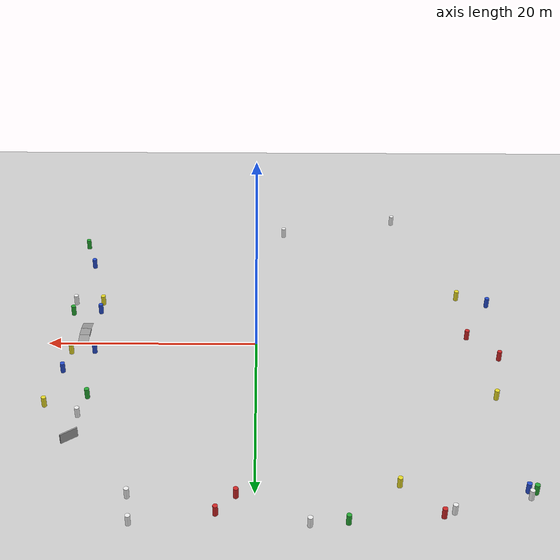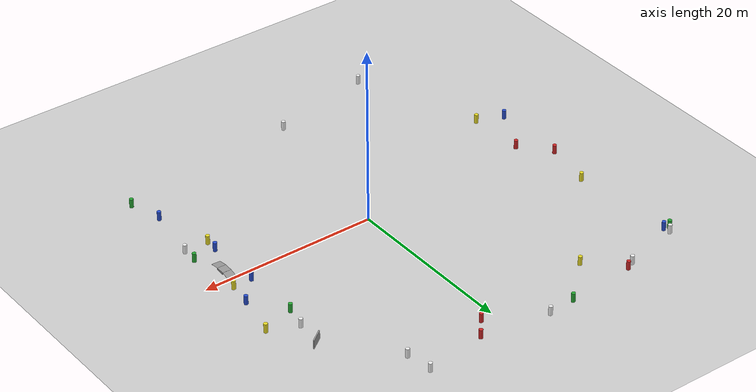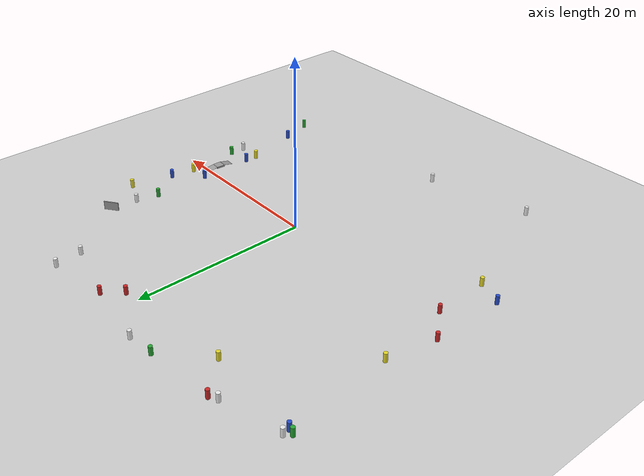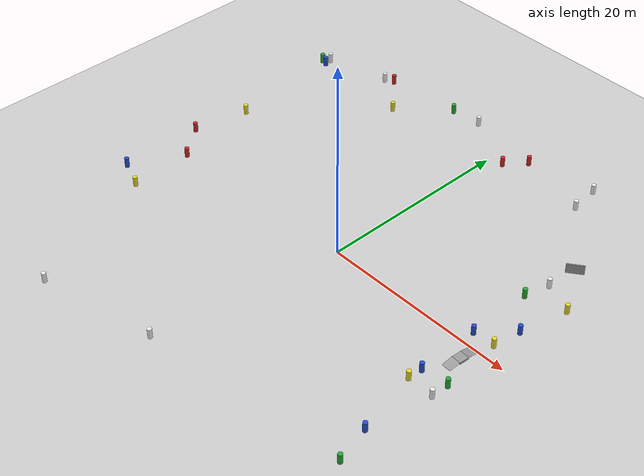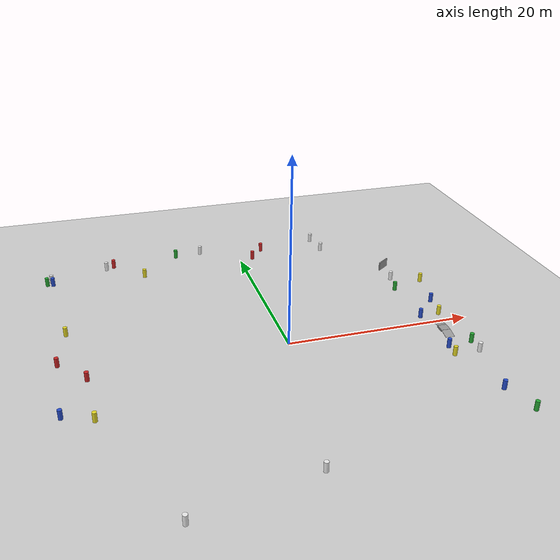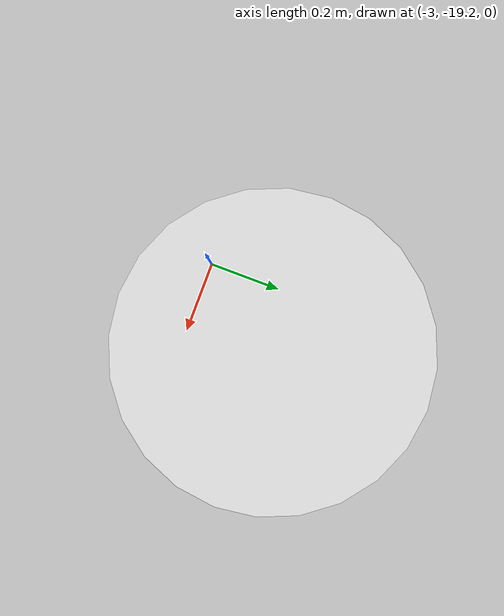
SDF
<sdf version="1.7">
 <world name="IGVC AutoNav">
  <light name="sun" type="directional">
   <pose>0 0 10 0 -0 0</pose>
   <diffuse>0.8 0.8 0.8 1</diffuse>
   <specular>0.2 0.2 0.2 1</specular>
   <attenuation>
    <range>1000</range>
    <constant>0.9</constant>
    <linear>0.01</linear>
    <quadratic>0.001</quadratic>
   </attenuation>
   <direction>-0.5 0.1 -0.9</direction>
   <spot><inner_angle>0</inner_angle><outer_angle>0</outer_angle><falloff>0</falloff></spot>
  </light>
  <model name="asphault_ground_plane">
   <static>1</static>
   <link name="link">
    <collision name="collision">
     <geometry><plane><normal>0 0 1</normal><size>100 100</size></plane></geometry>
     <surface><friction><ode><mu>100</mu><mu2>50</mu2></ode></friction></surface>
    </collision>
    <visual name="visual">
     <cast_shadows>0</cast_shadows>
     <geometry><plane><normal>0 0 1</normal><size>52 52</size></plane></geometry>
     <material>
      <script>
       <uri>/home/govind/abhiyaan/gazebo_ws/src/model_pkg/models/asphault_ground_plane/materials/scripts</uri>
       <uri>/home/govind/abhiyaan/gazebo_ws/src/model_pkg/models/asphault_ground_plane/materials/textures</uri>
       <name>AsphaultPlane/Image</name>
      </script>
     </material>
    </visual>
   </link>
  </model>
  <gravity>0 0 -9.8</gravity>
  <magnetic_field>6e-06 2.3e-05 -4.2e-05</magnetic_field>
  <atmosphere type="adiabatic"/>
  <physics type="ode">
   <max_step_size>0.001</max_step_size>
   <real_time_factor>1</real_time_factor>
   <real_time_update_rate>1000</real_time_update_rate>
  </physics>
  <scene><ambient>0.4 0.4 0.4 1</ambient><background>0.7 0.7 0.7 1</background><shadows>1</shadows></scene>
  <spherical_coordinates>
   <surface_model>EARTH_WGS84</surface_model>
   <latitude_deg>0</latitude_deg>
   <longitude_deg>0</longitude_deg>
   <elevation>0</elevation>
   <heading_deg>0</heading_deg>
  </spherical_coordinates>
  <model name="barrel">
   <link name="link">
    <inertial>
     <mass>1</mass>
     <inertia><ixx>0.145833</ixx><ixy>0</ixy><ixz>0</ixz><iyy>0.145833</iyy><iyz>0</iyz><izz>0.125</izz></inertia>
    </inertial>
    <visual name="visual">
     <geometry><cylinder><radius>0.222916</radius><length>1.03567</length></cylinder></geometry>
     <material>
      <script><name>Gazebo/Blue</name><uri>file://media/materials/scripts/gazebo.material</uri></script>
      <shader type="pixel"/>
     </material>
    </visual>
    <collision name="collision">
     <geometry><cylinder><radius>0.222916</radius><length>1.03567</length></cylinder></geometry>
     <surface>
      <friction>
       <ode><mu>1</mu><mu2>1</mu2><fdir1>0 0 0</fdir1><slip1>0</slip1><slip2>0</slip2></ode>
       <torsional>
        <coefficient>1</coefficient>
        <patch_radius>0</patch_radius>
        <surface_radius>0</surface_radius>
        <use_patch_radius>1</use_patch_radius>
        <ode><slip>0</slip></ode>
       </torsional>
      </friction>
      <bounce><restitution_coefficient>0</restitution_coefficient><threshold>1e+06</threshold></bounce>
      <contact>
       <collide_without_contact>0</collide_without_contact>
       <collide_without_contact_bitmask>1</collide_without_contact_bitmask>
       <collide_bitmask>1</collide_bitmask>
       <ode>
        <soft_cfm>0</soft_cfm>
        <soft_erp>0.2</soft_erp>
        <kp>1e+13</kp>
        <kd>1</kd>
        <max_vel>0.01</max_vel>
        <min_depth>0</min_depth>
       </ode>
       <bullet>
        <split_impulse>1</split_impulse>
        <split_impulse_penetration_threshold>-0.01</split_impulse_penetration_threshold>
        <soft_cfm>0</soft_cfm>
        <soft_erp>0.2</soft_erp>
        <kp>1e+13</kp>
        <kd>1</kd>
       </bullet>
      </contact>
     </surface>
    </collision>
   </link>
   <static>0</static>
   <pose>17.0065 -12.8825 0.517826 0 -0 0.000365</pose>
  </model>
  <model name="barrel_0">
   <link name="link">
    <inertial>
     <mass>1</mass>
     <inertia><ixx>0.145833</ixx><ixy>0</ixy><ixz>0</ixz><iyy>0.145833</iyy><iyz>0</iyz><izz>0.125</izz></inertia>
    </inertial>
    <visual name="visual">
     <geometry><cylinder><radius>0.222916</radius><length>1.03567</length></cylinder></geometry>
     <material>
      <script><name>Gazebo/Green</name><uri>file://media/materials/scripts/gazebo.material</uri></script>
      <shader type="pixel"/>
     </material>
    </visual>
    <collision name="collision">
     <geometry><cylinder><radius>0.222916</radius><length>1.03567</length></cylinder></geometry>
     <surface>
      <friction>
       <ode><mu>1</mu><mu2>1</mu2><fdir1>0 0 0</fdir1><slip1>0</slip1><slip2>0</slip2></ode>
       <torsional>
        <coefficient>1</coefficient>
        <patch_radius>0</patch_radius>
        <surface_radius>0</surface_radius>
        <use_patch_radius>1</use_patch_radius>
        <ode><slip>0</slip></ode>
       </torsional>
      </friction>
      <bounce><restitution_coefficient>0</restitution_coefficient><threshold>1e+06</threshold></bounce>
      <contact>
       <collide_without_contact>0</collide_without_contact>
       <collide_without_contact_bitmask>1</collide_without_contact_bitmask>
       <collide_bitmask>1</collide_bitmask>
       <ode>
        <soft_cfm>0</soft_cfm>
        <soft_erp>0.2</soft_erp>
        <kp>1e+13</kp>
        <kd>1</kd>
        <max_vel>0.01</max_vel>
        <min_depth>0</min_depth>
       </ode>
       <bullet>
        <split_impulse>1</split_impulse>
        <split_impulse_penetration_threshold>-0.01</split_impulse_penetration_threshold>
        <soft_cfm>0</soft_cfm>
        <soft_erp>0.2</soft_erp>
        <kp>1e+13</kp>
        <kd>1</kd>
       </bullet>
      </contact>
     </surface>
    </collision>
   </link>
   <static>0</static>
   <pose>18.0196 -16.5153 0.517825 0 -0 0.000403</pose>
  </model>
  <model name="barrel_3">
   <link name="link">
    <inertial>
     <mass>1</mass>
     <inertia><ixx>0.145833</ixx><ixy>0</ixy><ixz>0</ixz><iyy>0.145833</iyy><iyz>0</iyz><izz>0.125</izz></inertia>
    </inertial>
    <visual name="visual">
     <geometry><cylinder><radius>0.222916</radius><length>1.03567</length></cylinder></geometry>
     <material>
      <script><name>Gazebo/White</name><uri>file://media/materials/scripts/gazebo.material</uri></script>
      <shader type="pixel"/>
     </material>
    </visual>
    <collision name="collision">
     <geometry><cylinder><radius>0.222916</radius><length>1.03567</length></cylinder></geometry>
     <surface>
      <friction>
       <ode><mu>1</mu><mu2>1</mu2><fdir1>0 0 0</fdir1><slip1>0</slip1><slip2>0</slip2></ode>
       <torsional>
        <coefficient>1</coefficient>
        <patch_radius>0</patch_radius>
        <surface_radius>0</surface_radius>
        <use_patch_radius>1</use_patch_radius>
        <ode><slip>0</slip></ode>
       </torsional>
      </friction>
      <bounce><restitution_coefficient>0</restitution_coefficient><threshold>1e+06</threshold></bounce>
      <contact>
       <collide_without_contact>0</collide_without_contact>
       <collide_without_contact_bitmask>1</collide_without_contact_bitmask>
       <collide_bitmask>1</collide_bitmask>
       <ode>
        <soft_cfm>0</soft_cfm>
        <soft_erp>0.2</soft_erp>
        <kp>1e+13</kp>
        <kd>1</kd>
        <max_vel>0.01</max_vel>
        <min_depth>0</min_depth>
       </ode>
       <bullet>
        <split_impulse>1</split_impulse>
        <split_impulse_penetration_threshold>-0.01</split_impulse_penetration_threshold>
        <soft_cfm>0</soft_cfm>
        <soft_erp>0.2</soft_erp>
        <kp>1e+13</kp>
        <kd>1</kd>
       </bullet>
      </contact>
     </surface>
    </collision>
   </link>
   <static>0</static>
   <pose>-2.81322 -18.945 0.517826 -1e-06 0 0.000418</pose>
  </model>
  <model name="barrel_4">
   <link name="link">
    <inertial>
     <mass>1</mass>
     <inertia><ixx>0.145833</ixx><ixy>0</ixy><ixz>0</ixz><iyy>0.145833</iyy><iyz>0</iyz><izz>0.125</izz></inertia>
    </inertial>
    <visual name="visual">
     <geometry><cylinder><radius>0.222916</radius><length>1.03567</length></cylinder></geometry>
     <material>
      <script><name>Gazebo/White</name><uri>file://media/materials/scripts/gazebo.material</uri></script>
      <shader type="pixel"/>
     </material>
    </visual>
    <collision name="collision">
     <geometry><cylinder><radius>0.222916</radius><length>1.03567</length></cylinder></geometry>
     <surface>
      <friction>
       <ode><mu>1</mu><mu2>1</mu2><fdir1>0 0 0</fdir1><slip1>0</slip1><slip2>0</slip2></ode>
       <torsional>
        <coefficient>1</coefficient>
        <patch_radius>0</patch_radius>
        <surface_radius>0</surface_radius>
        <use_patch_radius>1</use_patch_radius>
        <ode><slip>0</slip></ode>
       </torsional>
      </friction>
      <bounce><restitution_coefficient>0</restitution_coefficient><threshold>1e+06</threshold></bounce>
      <contact>
       <collide_without_contact>0</collide_without_contact>
       <collide_without_contact_bitmask>1</collide_without_contact_bitmask>
       <collide_bitmask>1</collide_bitmask>
       <ode>
        <soft_cfm>0</soft_cfm>
        <soft_erp>0.2</soft_erp>
        <kp>1e+13</kp>
        <kd>1</kd>
        <max_vel>0.01</max_vel>
        <min_depth>0</min_depth>
       </ode>
       <bullet>
        <split_impulse>1</split_impulse>
        <split_impulse_penetration_threshold>-0.01</split_impulse_penetration_threshold>
        <soft_cfm>0</soft_cfm>
        <soft_erp>0.2</soft_erp>
        <kp>1e+13</kp>
        <kd>1</kd>
       </bullet>
      </contact>
     </surface>
    </collision>
   </link>
   <static>0</static>
   <pose>-14.6801 -21.5129 0.517826 0 -0 0.000377</pose>
  </model>
  <model name="barrel_5">
   <link name="link">
    <inertial>
     <mass>1</mass>
     <inertia><ixx>0.145833</ixx><ixy>0</ixy><ixz>0</ixz><iyy>0.145833</iyy><iyz>0</iyz><izz>0.125</izz></inertia>
    </inertial>
    <visual name="visual">
     <geometry><cylinder><radius>0.222916</radius><length>1.03567</length></cylinder></geometry>
     <material>
      <script><name>Gazebo/Yellow</name><uri>file://media/materials/scripts/gazebo.material</uri></script>
      <shader type="pixel"/>
     </material>
    </visual>
    <collision name="collision">
     <geometry><cylinder><radius>0.222916</radius><length>1.03567</length></cylinder></geometry>
     <surface>
      <friction>
       <ode><mu>1</mu><mu2>1</mu2><fdir1>0 0 0</fdir1><slip1>0</slip1><slip2>0</slip2></ode>
       <torsional>
        <coefficient>1</coefficient>
        <patch_radius>0</patch_radius>
        <surface_radius>0</surface_radius>
        <use_patch_radius>1</use_patch_radius>
        <ode><slip>0</slip></ode>
       </torsional>
      </friction>
      <bounce><restitution_coefficient>0</restitution_coefficient><threshold>1e+06</threshold></bounce>
      <contact>
       <collide_without_contact>0</collide_without_contact>
       <collide_without_contact_bitmask>1</collide_without_contact_bitmask>
       <collide_bitmask>1</collide_bitmask>
       <ode>
        <soft_cfm>0</soft_cfm>
        <soft_erp>0.2</soft_erp>
        <kp>1e+13</kp>
        <kd>1</kd>
        <max_vel>0.01</max_vel>
        <min_depth>0</min_depth>
       </ode>
       <bullet>
        <split_impulse>1</split_impulse>
        <split_impulse_penetration_threshold>-0.01</split_impulse_penetration_threshold>
        <soft_cfm>0</soft_cfm>
        <soft_erp>0.2</soft_erp>
        <kp>1e+13</kp>
        <kd>1</kd>
       </bullet>
      </contact>
     </surface>
    </collision>
   </link>
   <static>0</static>
   <pose>-21.8934 7.82003 0.517826 0 -0 0.000413</pose>
  </model>
  <model name="barrel_7">
   <link name="link">
    <inertial>
     <mass>1</mass>
     <inertia><ixx>0.145833</ixx><ixy>0</ixy><ixz>0</ixz><iyy>0.145833</iyy><iyz>0</iyz><izz>0.125</izz></inertia>
    </inertial>
    <visual name="visual">
     <geometry><cylinder><radius>0.222916</radius><length>1.03567</length></cylinder></geometry>
     <material>
      <script><name>Gazebo/Blue</name><uri>file://media/materials/scripts/gazebo.material</uri></script>
      <shader type="pixel"/>
     </material>
    </visual>
    <collision name="collision">
     <geometry><cylinder><radius>0.222916</radius><length>1.03567</length></cylinder></geometry>
     <surface>
      <friction>
       <ode><mu>1</mu><mu2>1</mu2><fdir1>0 0 0</fdir1><slip1>0</slip1><slip2>0</slip2></ode>
       <torsional>
        <coefficient>1</coefficient>
        <patch_radius>0</patch_radius>
        <surface_radius>0</surface_radius>
        <use_patch_radius>1</use_patch_radius>
        <ode><slip>0</slip></ode>
       </torsional>
      </friction>
      <bounce><restitution_coefficient>0</restitution_coefficient><threshold>1e+06</threshold></bounce>
      <contact>
       <collide_without_contact>0</collide_without_contact>
       <collide_without_contact_bitmask>1</collide_without_contact_bitmask>
       <collide_bitmask>1</collide_bitmask>
       <ode>
        <soft_cfm>0</soft_cfm>
        <soft_erp>0.2</soft_erp>
        <kp>1e+13</kp>
        <kd>1</kd>
        <max_vel>0.01</max_vel>
        <min_depth>0</min_depth>
       </ode>
       <bullet>
        <split_impulse>1</split_impulse>
        <split_impulse_penetration_threshold>-0.01</split_impulse_penetration_threshold>
        <soft_cfm>0</soft_cfm>
        <soft_erp>0.2</soft_erp>
        <kp>1e+13</kp>
        <kd>1</kd>
       </bullet>
      </contact>
     </surface>
    </collision>
   </link>
   <static>0</static>
   <pose>-22.997 -6.29974 0.517834 -1e-06 1e-06 0.00037</pose>
  </model>
  <model name="barrel_8">
   <link name="link">
    <inertial>
     <mass>1</mass>
     <inertia><ixx>0.145833</ixx><ixy>0</ixy><ixz>0</ixz><iyy>0.145833</iyy><iyz>0</iyz><izz>0.125</izz></inertia>
    </inertial>
    <visual name="visual">
     <geometry><cylinder><radius>0.222916</radius><length>1.03567</length></cylinder></geometry>
     <material>
      <script><name>Gazebo/White</name><uri>file://media/materials/scripts/gazebo.material</uri></script>
      <shader type="pixel"/>
     </material>
    </visual>
    <collision name="collision">
     <geometry><cylinder><radius>0.222916</radius><length>1.03567</length></cylinder></geometry>
     <surface>
      <friction>
       <ode><mu>1</mu><mu2>1</mu2><fdir1>0 0 0</fdir1><slip1>0</slip1><slip2>0</slip2></ode>
       <torsional>
        <coefficient>1</coefficient>
        <patch_radius>0</patch_radius>
        <surface_radius>0</surface_radius>
        <use_patch_radius>1</use_patch_radius>
        <ode><slip>0</slip></ode>
       </torsional>
      </friction>
      <bounce><restitution_coefficient>0</restitution_coefficient><threshold>1e+06</threshold></bounce>
      <contact>
       <collide_without_contact>0</collide_without_contact>
       <collide_without_contact_bitmask>1</collide_without_contact_bitmask>
       <collide_bitmask>1</collide_bitmask>
       <ode>
        <soft_cfm>0</soft_cfm>
        <soft_erp>0.2</soft_erp>
        <kp>1e+13</kp>
        <kd>1</kd>
        <max_vel>0.01</max_vel>
        <min_depth>0</min_depth>
       </ode>
       <bullet>
        <split_impulse>1</split_impulse>
        <split_impulse_penetration_threshold>-0.01</split_impulse_penetration_threshold>
        <soft_cfm>0</soft_cfm>
        <soft_erp>0.2</soft_erp>
        <kp>1e+13</kp>
        <kd>1</kd>
       </bullet>
      </contact>
     </surface>
    </collision>
   </link>
   <static>0</static>
   <pose>-22.9019 20.4353 0.517834 1e-06 -0 0.000352</pose>
  </model>
  <model name="barrel_10">
   <link name="link">
    <inertial>
     <mass>1</mass>
     <inertia><ixx>0.145833</ixx><ixy>0</ixy><ixz>0</ixz><iyy>0.145833</iyy><iyz>0</iyz><izz>0.125</izz></inertia>
    </inertial>
    <visual name="visual">
     <geometry><cylinder><radius>0.222916</radius><length>1.03567</length></cylinder></geometry>
     <material>
      <script><name>Gazebo/Blue</name><uri>file://media/materials/scripts/gazebo.material</uri></script>
      <shader type="pixel"/>
     </material>
    </visual>
    <collision name="collision">
     <geometry><cylinder><radius>0.222916</radius><length>1.03567</length></cylinder></geometry>
     <surface>
      <friction>
       <ode><mu>1</mu><mu2>1</mu2><fdir1>0 0 0</fdir1><slip1>0</slip1><slip2>0</slip2></ode>
       <torsional>
        <coefficient>1</coefficient>
        <patch_radius>0</patch_radius>
        <surface_radius>0</surface_radius>
        <use_patch_radius>1</use_patch_radius>
        <ode><slip>0</slip></ode>
       </torsional>
      </friction>
      <bounce><restitution_coefficient>0</restitution_coefficient><threshold>1e+06</threshold></bounce>
      <contact>
       <collide_without_contact>0</collide_without_contact>
       <collide_without_contact_bitmask>1</collide_without_contact_bitmask>
       <collide_bitmask>1</collide_bitmask>
       <ode>
        <soft_cfm>0</soft_cfm>
        <soft_erp>0.2</soft_erp>
        <kp>1e+13</kp>
        <kd>1</kd>
        <max_vel>0.01</max_vel>
        <min_depth>0</min_depth>
       </ode>
       <bullet>
        <split_impulse>1</split_impulse>
        <split_impulse_penetration_threshold>-0.01</split_impulse_penetration_threshold>
        <soft_cfm>0</soft_cfm>
        <soft_erp>0.2</soft_erp>
        <kp>1e+13</kp>
        <kd>1</kd>
       </bullet>
      </contact>
     </surface>
    </collision>
   </link>
   <static>0</static>
   <pose>-22.7816 19.6452 0.517834 1e-06 0 0.000371</pose>
  </model>
  <model name="barrel_11">
   <link name="link">
    <inertial>
     <mass>1</mass>
     <inertia><ixx>0.145833</ixx><ixy>0</ixy><ixz>0</ixz><iyy>0.145833</iyy><iyz>0</iyz><izz>0.125</izz></inertia>
    </inertial>
    <visual name="visual">
     <geometry><cylinder><radius>0.222916</radius><length>1.03567</length></cylinder></geometry>
     <material>
      <script><name>Gazebo/Yellow</name><uri>file://media/materials/scripts/gazebo.material</uri></script>
      <shader type="pixel"/>
     </material>
    </visual>
    <collision name="collision">
     <geometry><cylinder><radius>0.222916</radius><length>1.03567</length></cylinder></geometry>
     <surface>
      <friction>
       <ode><mu>1</mu><mu2>1</mu2><fdir1>0 0 0</fdir1><slip1>0</slip1><slip2>0</slip2></ode>
       <torsional>
        <coefficient>1</coefficient>
        <patch_radius>0</patch_radius>
        <surface_radius>0</surface_radius>
        <use_patch_radius>1</use_patch_radius>
        <ode><slip>0</slip></ode>
       </torsional>
      </friction>
      <bounce><restitution_coefficient>0</restitution_coefficient><threshold>1e+06</threshold></bounce>
      <contact>
       <collide_without_contact>0</collide_without_contact>
       <collide_without_contact_bitmask>1</collide_without_contact_bitmask>
       <collide_bitmask>1</collide_bitmask>
       <ode>
        <soft_cfm>0</soft_cfm>
        <soft_erp>0.2</soft_erp>
        <kp>1e+13</kp>
        <kd>1</kd>
        <max_vel>0.01</max_vel>
        <min_depth>0</min_depth>
       </ode>
       <bullet>
        <split_impulse>1</split_impulse>
        <split_impulse_penetration_threshold>-0.01</split_impulse_penetration_threshold>
        <soft_cfm>0</soft_cfm>
        <soft_erp>0.2</soft_erp>
        <kp>1e+13</kp>
        <kd>1</kd>
       </bullet>
      </contact>
     </surface>
    </collision>
   </link>
   <static>0</static>
   <pose>-20.098 -7.4723 0.517834 1e-06 -0 0.000346</pose>
  </model>
  <model name="barrel_13">
   <link name="link">
    <inertial>
     <mass>1</mass>
     <inertia><ixx>0.145833</ixx><ixy>0</ixy><ixz>0</ixz><iyy>0.145833</iyy><iyz>0</iyz><izz>0.125</izz></inertia>
    </inertial>
    <visual name="visual">
     <geometry><cylinder><radius>0.222916</radius><length>1.03567</length></cylinder></geometry>
     <material>
      <script><name>Gazebo/Green</name><uri>file://media/materials/scripts/gazebo.material</uri></script>
      <shader type="pixel"/>
     </material>
    </visual>
    <collision name="collision">
     <geometry><cylinder><radius>0.222916</radius><length>1.03567</length></cylinder></geometry>
     <surface>
      <friction>
       <ode><mu>1</mu><mu2>1</mu2><fdir1>0 0 0</fdir1><slip1>0</slip1><slip2>0</slip2></ode>
       <torsional>
        <coefficient>1</coefficient>
        <patch_radius>0</patch_radius>
        <surface_radius>0</surface_radius>
        <use_patch_radius>1</use_patch_radius>
        <ode><slip>0</slip></ode>
       </torsional>
      </friction>
      <bounce><restitution_coefficient>0</restitution_coefficient><threshold>1e+06</threshold></bounce>
      <contact>
       <collide_without_contact>0</collide_without_contact>
       <collide_without_contact_bitmask>1</collide_without_contact_bitmask>
       <collide_bitmask>1</collide_bitmask>
       <ode>
        <soft_cfm>0</soft_cfm>
        <soft_erp>0.2</soft_erp>
        <kp>1e+13</kp>
        <kd>1</kd>
        <max_vel>0.01</max_vel>
        <min_depth>0</min_depth>
       </ode>
       <bullet>
        <split_impulse>1</split_impulse>
        <split_impulse_penetration_threshold>-0.01</split_impulse_penetration_threshold>
        <soft_cfm>0</soft_cfm>
        <soft_erp>0.2</soft_erp>
        <kp>1e+13</kp>
        <kd>1</kd>
       </bullet>
      </contact>
     </surface>
    </collision>
   </link>
   <static>0</static>
   <pose>-23.4206 19.804 0.517834 1e-06 -0 0.000338</pose>
  </model>
  <model name="barrel_14">
   <link name="link">
    <inertial>
     <mass>1</mass>
     <inertia><ixx>0.145833</ixx><ixy>0</ixy><ixz>0</ixz><iyy>0.145833</iyy><iyz>0</iyz><izz>0.125</izz></inertia>
    </inertial>
    <visual name="visual">
     <geometry><cylinder><radius>0.222916</radius><length>1.03567</length></cylinder></geometry>
     <material>
      <script><name>Gazebo/Red</name><uri>file://media/materials/scripts/gazebo.material</uri></script>
      <shader type="pixel"/>
     </material>
    </visual>
    <collision name="collision">
     <geometry><cylinder><radius>0.222916</radius><length>1.03567</length></cylinder></geometry>
     <surface>
      <friction>
       <ode><mu>1</mu><mu2>1</mu2><fdir1>0 0 0</fdir1><slip1>0</slip1><slip2>0</slip2></ode>
       <torsional>
        <coefficient>1</coefficient>
        <patch_radius>0</patch_radius>
        <surface_radius>0</surface_radius>
        <use_patch_radius>1</use_patch_radius>
        <ode><slip>0</slip></ode>
       </torsional>
      </friction>
      <bounce><restitution_coefficient>0</restitution_coefficient><threshold>1e+06</threshold></bounce>
      <contact>
       <collide_without_contact>0</collide_without_contact>
       <collide_without_contact_bitmask>1</collide_without_contact_bitmask>
       <collide_bitmask>1</collide_bitmask>
       <ode>
        <soft_cfm>0</soft_cfm>
        <soft_erp>0.2</soft_erp>
        <kp>1e+13</kp>
        <kd>1</kd>
        <max_vel>0.01</max_vel>
        <min_depth>0</min_depth>
       </ode>
       <bullet>
        <split_impulse>1</split_impulse>
        <split_impulse_penetration_threshold>-0.01</split_impulse_penetration_threshold>
        <soft_cfm>0</soft_cfm>
        <soft_erp>0.2</soft_erp>
        <kp>1e+13</kp>
        <kd>1</kd>
       </bullet>
      </contact>
     </surface>
    </collision>
   </link>
   <static>0</static>
   <pose>-15.4557 22.566 0.517834 1e-06 0 0.000371</pose>
  </model>
  <model name="barrel_15">
   <link name="link">
    <inertial>
     <mass>1</mass>
     <inertia><ixx>0.145833</ixx><ixy>0</ixy><ixz>0</ixz><iyy>0.145833</iyy><iyz>0</iyz><izz>0.125</izz></inertia>
    </inertial>
    <visual name="visual">
     <geometry><cylinder><radius>0.222916</radius><length>1.03567</length></cylinder></geometry>
     <material>
      <script><name>Gazebo/White</name><uri>file://media/materials/scripts/gazebo.material</uri></script>
      <shader type="pixel"/>
     </material>
    </visual>
    <collision name="collision">
     <geometry><cylinder><radius>0.222916</radius><length>1.03567</length></cylinder></geometry>
     <surface>
      <friction>
       <ode><mu>1</mu><mu2>1</mu2><fdir1>0 0 0</fdir1><slip1>0</slip1><slip2>0</slip2></ode>
       <torsional>
        <coefficient>1</coefficient>
        <patch_radius>0</patch_radius>
        <surface_radius>0</surface_radius>
        <use_patch_radius>1</use_patch_radius>
        <ode><slip>0</slip></ode>
       </torsional>
      </friction>
      <bounce><restitution_coefficient>0</restitution_coefficient><threshold>1e+06</threshold></bounce>
      <contact>
       <collide_without_contact>0</collide_without_contact>
       <collide_without_contact_bitmask>1</collide_without_contact_bitmask>
       <collide_bitmask>1</collide_bitmask>
       <ode>
        <soft_cfm>0</soft_cfm>
        <soft_erp>0.2</soft_erp>
        <kp>1e+13</kp>
        <kd>1</kd>
        <max_vel>0.01</max_vel>
        <min_depth>0</min_depth>
       </ode>
       <bullet>
        <split_impulse>1</split_impulse>
        <split_impulse_penetration_threshold>-0.01</split_impulse_penetration_threshold>
        <soft_cfm>0</soft_cfm>
        <soft_erp>0.2</soft_erp>
        <kp>1e+13</kp>
        <kd>1</kd>
       </bullet>
      </contact>
     </surface>
    </collision>
   </link>
   <static>0</static>
   <pose>-16.3625 22.1169 0.517834 1e-06 -0 0.000412</pose>
  </model>
  <model name="barrel_16">
   <link name="link">
    <inertial>
     <mass>1</mass>
     <inertia><ixx>0.145833</ixx><ixy>0</ixy><ixz>0</ixz><iyy>0.145833</iyy><iyz>0</iyz><izz>0.125</izz></inertia>
    </inertial>
    <visual name="visual">
     <geometry><cylinder><radius>0.222916</radius><length>1.03567</length></cylinder></geometry>
     <material>
      <script><name>Gazebo/Yellow</name><uri>file://media/materials/scripts/gazebo.material</uri></script>
      <shader type="pixel"/>
     </material>
    </visual>
    <collision name="collision">
     <geometry><cylinder><radius>0.222916</radius><length>1.03567</length></cylinder></geometry>
     <surface>
      <friction>
       <ode><mu>1</mu><mu2>1</mu2><fdir1>0 0 0</fdir1><slip1>0</slip1><slip2>0</slip2></ode>
       <torsional>
        <coefficient>1</coefficient>
        <patch_radius>0</patch_radius>
        <surface_radius>0</surface_radius>
        <use_patch_radius>1</use_patch_radius>
        <ode><slip>0</slip></ode>
       </torsional>
      </friction>
      <bounce><restitution_coefficient>0</restitution_coefficient><threshold>1e+06</threshold></bounce>
      <contact>
       <collide_without_contact>0</collide_without_contact>
       <collide_without_contact_bitmask>1</collide_without_contact_bitmask>
       <collide_bitmask>1</collide_bitmask>
       <ode>
        <soft_cfm>0</soft_cfm>
        <soft_erp>0.2</soft_erp>
        <kp>1e+13</kp>
        <kd>1</kd>
        <max_vel>0.01</max_vel>
        <min_depth>0</min_depth>
       </ode>
       <bullet>
        <split_impulse>1</split_impulse>
        <split_impulse_penetration_threshold>-0.01</split_impulse_penetration_threshold>
        <soft_cfm>0</soft_cfm>
        <soft_erp>0.2</soft_erp>
        <kp>1e+13</kp>
        <kd>1</kd>
       </bullet>
      </contact>
     </surface>
    </collision>
   </link>
   <static>0</static>
   <pose>-12.1316 19.06 0.517834 1e-06 -0 0.001551</pose>
  </model>
  <model name="barrel_22">
   <link name="link">
    <inertial>
     <mass>1</mass>
     <inertia><ixx>0.145833</ixx><ixy>0</ixy><ixz>0</ixz><iyy>0.145833</iyy><iyz>0</iyz><izz>0.125</izz></inertia>
    </inertial>
    <visual name="visual">
     <geometry><cylinder><radius>0.222916</radius><length>1.03567</length></cylinder></geometry>
     <material>
      <script><name>Gazebo/White</name><uri>file://media/materials/scripts/gazebo.material</uri></script>
      <shader type="pixel"/>
     </material>
    </visual>
    <collision name="collision">
     <geometry><cylinder><radius>0.222916</radius><length>1.03567</length></cylinder></geometry>
     <surface>
      <friction>
       <ode><mu>1</mu><mu2>1</mu2><fdir1>0 0 0</fdir1><slip1>0</slip1><slip2>0</slip2></ode>
       <torsional>
        <coefficient>1</coefficient>
        <patch_radius>0</patch_radius>
        <surface_radius>0</surface_radius>
        <use_patch_radius>1</use_patch_radius>
        <ode><slip>0</slip></ode>
       </torsional>
      </friction>
      <bounce><restitution_coefficient>0</restitution_coefficient><threshold>1e+06</threshold></bounce>
      <contact>
       <collide_without_contact>0</collide_without_contact>
       <collide_without_contact_bitmask>1</collide_without_contact_bitmask>
       <collide_bitmask>1</collide_bitmask>
       <ode>
        <soft_cfm>0</soft_cfm>
        <soft_erp>0.2</soft_erp>
        <kp>1e+13</kp>
        <kd>1</kd>
        <max_vel>0.01</max_vel>
        <min_depth>0</min_depth>
       </ode>
       <bullet>
        <split_impulse>1</split_impulse>
        <split_impulse_penetration_threshold>-0.01</split_impulse_penetration_threshold>
        <soft_cfm>0</soft_cfm>
        <soft_erp>0.2</soft_erp>
        <kp>1e+13</kp>
        <kd>1</kd>
       </bullet>
      </contact>
     </surface>
    </collision>
   </link>
   <static>0</static>
   <pose>-4.48687 23.6095 0.517826 0 -0 0.000235</pose>
  </model>
  <model name="barrel_23">
   <link name="link">
    <inertial>
     <mass>1</mass>
     <inertia><ixx>0.145833</ixx><ixy>0</ixy><ixz>0</ixz><iyy>0.145833</iyy><iyz>0</iyz><izz>0.125</izz></inertia>
    </inertial>
    <visual name="visual">
     <geometry><cylinder><radius>0.222916</radius><length>1.03567</length></cylinder></geometry>
     <material>
      <script><name>Gazebo/Green</name><uri>file://media/materials/scripts/gazebo.material</uri></script>
      <shader type="pixel"/>
     </material>
    </visual>
    <collision name="collision">
     <geometry><cylinder><radius>0.222916</radius><length>1.03567</length></cylinder></geometry>
     <surface>
      <friction>
       <ode><mu>1</mu><mu2>1</mu2><fdir1>0 0 0</fdir1><slip1>0</slip1><slip2>0</slip2></ode>
       <torsional>
        <coefficient>1</coefficient>
        <patch_radius>0</patch_radius>
        <surface_radius>0</surface_radius>
        <use_patch_radius>1</use_patch_radius>
        <ode><slip>0</slip></ode>
       </torsional>
      </friction>
      <bounce><restitution_coefficient>0</restitution_coefficient><threshold>1e+06</threshold></bounce>
      <contact>
       <collide_without_contact>0</collide_without_contact>
       <collide_without_contact_bitmask>1</collide_without_contact_bitmask>
       <collide_bitmask>1</collide_bitmask>
       <ode>
        <soft_cfm>0</soft_cfm>
        <soft_erp>0.2</soft_erp>
        <kp>1e+13</kp>
        <kd>1</kd>
        <max_vel>0.01</max_vel>
        <min_depth>0</min_depth>
       </ode>
       <bullet>
        <split_impulse>1</split_impulse>
        <split_impulse_penetration_threshold>-0.01</split_impulse_penetration_threshold>
        <soft_cfm>0</soft_cfm>
        <soft_erp>0.2</soft_erp>
        <kp>1e+13</kp>
        <kd>1</kd>
       </bullet>
      </contact>
     </surface>
    </collision>
   </link>
   <static>0</static>
   <pose>-7.63439 23.3241 0.517826 -1e-06 -0 0.00034</pose>
  </model>
  <model name="barrel_24">
   <link name="link">
    <inertial>
     <mass>1</mass>
     <inertia><ixx>0.145833</ixx><ixy>0</ixy><ixz>0</ixz><iyy>0.145833</iyy><iyz>0</iyz><izz>0.125</izz></inertia>
    </inertial>
    <visual name="visual">
     <geometry><cylinder><radius>0.222916</radius><length>1.03567</length></cylinder></geometry>
     <material>
      <script><name>Gazebo/White</name><uri>file://media/materials/scripts/gazebo.material</uri></script>
      <shader type="pixel"/>
     </material>
    </visual>
    <collision name="collision">
     <geometry><cylinder><radius>0.222916</radius><length>1.03567</length></cylinder></geometry>
     <surface>
      <friction>
       <ode><mu>1</mu><mu2>1</mu2><fdir1>0 0 0</fdir1><slip1>0</slip1><slip2>0</slip2></ode>
       <torsional>
        <coefficient>1</coefficient>
        <patch_radius>0</patch_radius>
        <surface_radius>0</surface_radius>
        <use_patch_radius>1</use_patch_radius>
        <ode><slip>0</slip></ode>
       </torsional>
      </friction>
      <bounce><restitution_coefficient>0</restitution_coefficient><threshold>1e+06</threshold></bounce>
      <contact>
       <collide_without_contact>0</collide_without_contact>
       <collide_without_contact_bitmask>1</collide_without_contact_bitmask>
       <collide_bitmask>1</collide_bitmask>
       <ode>
        <soft_cfm>0</soft_cfm>
        <soft_erp>0.2</soft_erp>
        <kp>1e+13</kp>
        <kd>1</kd>
        <max_vel>0.01</max_vel>
        <min_depth>0</min_depth>
       </ode>
       <bullet>
        <split_impulse>1</split_impulse>
        <split_impulse_penetration_threshold>-0.01</split_impulse_penetration_threshold>
        <soft_cfm>0</soft_cfm>
        <soft_erp>0.2</soft_erp>
        <kp>1e+13</kp>
        <kd>1</kd>
       </bullet>
      </contact>
     </surface>
    </collision>
   </link>
   <static>0</static>
   <pose>10.2563 23.5261 0.517825 0 -0 0.000138</pose>
  </model>
  <model name="barrel_26">
   <link name="link">
    <inertial>
     <mass>1</mass>
     <inertia><ixx>0.145833</ixx><ixy>0</ixy><ixz>0</ixz><iyy>0.145833</iyy><iyz>0</iyz><izz>0.125</izz></inertia>
    </inertial>
    <visual name="visual">
     <geometry><cylinder><radius>0.222916</radius><length>1.03567</length></cylinder></geometry>
     <material>
      <script><name>Gazebo/Red</name><uri>file://media/materials/scripts/gazebo.material</uri></script>
      <shader type="pixel"/>
     </material>
    </visual>
    <collision name="collision">
     <geometry><cylinder><radius>0.222916</radius><length>1.03567</length></cylinder></geometry>
     <surface>
      <friction>
       <ode><mu>1</mu><mu2>1</mu2><fdir1>0 0 0</fdir1><slip1>0</slip1><slip2>0</slip2></ode>
       <torsional>
        <coefficient>1</coefficient>
        <patch_radius>0</patch_radius>
        <surface_radius>0</surface_radius>
        <use_patch_radius>1</use_patch_radius>
        <ode><slip>0</slip></ode>
       </torsional>
      </friction>
      <bounce><restitution_coefficient>0</restitution_coefficient><threshold>1e+06</threshold></bounce>
      <contact>
       <collide_without_contact>0</collide_without_contact>
       <collide_without_contact_bitmask>1</collide_without_contact_bitmask>
       <collide_bitmask>1</collide_bitmask>
       <ode>
        <soft_cfm>0</soft_cfm>
        <soft_erp>0.2</soft_erp>
        <kp>1e+13</kp>
        <kd>1</kd>
        <max_vel>0.01</max_vel>
        <min_depth>0</min_depth>
       </ode>
       <bullet>
        <split_impulse>1</split_impulse>
        <split_impulse_penetration_threshold>-0.01</split_impulse_penetration_threshold>
        <soft_cfm>0</soft_cfm>
        <soft_erp>0.2</soft_erp>
        <kp>1e+13</kp>
        <kd>1</kd>
       </bullet>
      </contact>
     </surface>
    </collision>
   </link>
   <static>0</static>
   <pose>1.58293 20.4113 0.517827 -1e-06 -1e-06 0.000364</pose>
  </model>
  <model name="barrel_27">
   <link name="link">
    <inertial>
     <mass>1</mass>
     <inertia><ixx>0.145833</ixx><ixy>0</ixy><ixz>0</ixz><iyy>0.145833</iyy><iyz>0</iyz><izz>0.125</izz></inertia>
    </inertial>
    <visual name="visual">
     <geometry><cylinder><radius>0.222916</radius><length>1.03567</length></cylinder></geometry>
     <material>
      <script><name>Gazebo/Red</name><uri>file://media/materials/scripts/gazebo.material</uri></script>
      <shader type="pixel"/>
     </material>
    </visual>
    <collision name="collision">
     <geometry><cylinder><radius>0.222916</radius><length>1.03567</length></cylinder></geometry>
     <surface>
      <friction>
       <ode><mu>1</mu><mu2>1</mu2><fdir1>0 0 0</fdir1><slip1>0</slip1><slip2>0</slip2></ode>
       <torsional>
        <coefficient>1</coefficient>
        <patch_radius>0</patch_radius>
        <surface_radius>0</surface_radius>
        <use_patch_radius>1</use_patch_radius>
        <ode><slip>0</slip></ode>
       </torsional>
      </friction>
      <bounce><restitution_coefficient>0</restitution_coefficient><threshold>1e+06</threshold></bounce>
      <contact>
       <collide_without_contact>0</collide_without_contact>
       <collide_without_contact_bitmask>1</collide_without_contact_bitmask>
       <collide_bitmask>1</collide_bitmask>
       <ode>
        <soft_cfm>0</soft_cfm>
        <soft_erp>0.2</soft_erp>
        <kp>1e+13</kp>
        <kd>1</kd>
        <max_vel>0.01</max_vel>
        <min_depth>0</min_depth>
       </ode>
       <bullet>
        <split_impulse>1</split_impulse>
        <split_impulse_penetration_threshold>-0.01</split_impulse_penetration_threshold>
        <soft_cfm>0</soft_cfm>
        <soft_erp>0.2</soft_erp>
        <kp>1e+13</kp>
        <kd>1</kd>
       </bullet>
      </contact>
     </surface>
    </collision>
   </link>
   <static>0</static>
   <pose>3.21879 22.403 0.517825 0 -0 0.000328</pose>
  </model>
  <model name="barrel_28">
   <link name="link">
    <inertial>
     <mass>1</mass>
     <inertia><ixx>0.145833</ixx><ixy>0</ixy><ixz>0</ixz><iyy>0.145833</iyy><iyz>0</iyz><izz>0.125</izz></inertia>
    </inertial>
    <visual name="visual">
     <geometry><cylinder><radius>0.222916</radius><length>1.03567</length></cylinder></geometry>
     <material>
      <script><name>Gazebo/White</name><uri>file://media/materials/scripts/gazebo.material</uri></script>
      <shader type="pixel"/>
     </material>
    </visual>
    <collision name="collision">
     <geometry><cylinder><radius>0.222916</radius><length>1.03567</length></cylinder></geometry>
     <surface>
      <friction>
       <ode><mu>1</mu><mu2>1</mu2><fdir1>0 0 0</fdir1><slip1>0</slip1><slip2>0</slip2></ode>
       <torsional>
        <coefficient>1</coefficient>
        <patch_radius>0</patch_radius>
        <surface_radius>0</surface_radius>
        <use_patch_radius>1</use_patch_radius>
        <ode><slip>0</slip></ode>
       </torsional>
      </friction>
      <bounce><restitution_coefficient>0</restitution_coefficient><threshold>1e+06</threshold></bounce>
      <contact>
       <collide_without_contact>0</collide_without_contact>
       <collide_without_contact_bitmask>1</collide_without_contact_bitmask>
       <collide_bitmask>1</collide_bitmask>
       <ode>
        <soft_cfm>0</soft_cfm>
        <soft_erp>0.2</soft_erp>
        <kp>1e+13</kp>
        <kd>1</kd>
        <max_vel>0.01</max_vel>
        <min_depth>0</min_depth>
       </ode>
       <bullet>
        <split_impulse>1</split_impulse>
        <split_impulse_penetration_threshold>-0.01</split_impulse_penetration_threshold>
        <soft_cfm>0</soft_cfm>
        <soft_erp>0.2</soft_erp>
        <kp>1e+13</kp>
        <kd>1</kd>
       </bullet>
      </contact>
     </surface>
    </collision>
   </link>
   <static>0</static>
   <pose>10.6368 20.4921 0.517826 -1e-06 -0 0.000304</pose>
  </model>
  <model name="barrel_30">
   <link name="link">
    <inertial>
     <mass>1</mass>
     <inertia><ixx>0.145833</ixx><ixy>0</ixy><ixz>0</ixz><iyy>0.145833</iyy><iyz>0</iyz><izz>0.125</izz></inertia>
    </inertial>
    <visual name="visual">
     <geometry><cylinder><radius>0.222916</radius><length>1.03567</length></cylinder></geometry>
     <material>
      <script><name>Gazebo/Green</name><uri>file://media/materials/scripts/gazebo.material</uri></script>
      <shader type="pixel"/>
     </material>
    </visual>
    <collision name="collision">
     <geometry><cylinder><radius>0.222916</radius><length>1.03567</length></cylinder></geometry>
     <surface>
      <friction>
       <ode><mu>1</mu><mu2>1</mu2><fdir1>0 0 0</fdir1><slip1>0</slip1><slip2>0</slip2></ode>
       <torsional>
        <coefficient>1</coefficient>
        <patch_radius>0</patch_radius>
        <surface_radius>0</surface_radius>
        <use_patch_radius>1</use_patch_radius>
        <ode><slip>0</slip></ode>
       </torsional>
      </friction>
      <bounce><restitution_coefficient>0</restitution_coefficient><threshold>1e+06</threshold></bounce>
      <contact>
       <collide_without_contact>0</collide_without_contact>
       <collide_without_contact_bitmask>1</collide_without_contact_bitmask>
       <collide_bitmask>1</collide_bitmask>
       <ode>
        <soft_cfm>0</soft_cfm>
        <soft_erp>0.2</soft_erp>
        <kp>1e+13</kp>
        <kd>1</kd>
        <max_vel>0.01</max_vel>
        <min_depth>0</min_depth>
       </ode>
       <bullet>
        <split_impulse>1</split_impulse>
        <split_impulse_penetration_threshold>-0.01</split_impulse_penetration_threshold>
        <soft_cfm>0</soft_cfm>
        <soft_erp>0.2</soft_erp>
        <kp>1e+13</kp>
        <kd>1</kd>
       </bullet>
      </contact>
     </surface>
    </collision>
   </link>
   <static>0</static>
   <pose>18.1831 -4.69047 0.517826 -1e-06 -0 0.000309</pose>
  </model>
  <model name="barrel_31">
   <link name="link">
    <inertial>
     <mass>1</mass>
     <inertia><ixx>0.145833</ixx><ixy>0</ixy><ixz>0</ixz><iyy>0.145833</iyy><iyz>0</iyz><izz>0.125</izz></inertia>
    </inertial>
    <visual name="visual">
     <geometry><cylinder><radius>0.222916</radius><length>1.03567</length></cylinder></geometry>
     <material>
      <script><name>Gazebo/Green</name><uri>file://media/materials/scripts/gazebo.material</uri></script>
      <shader type="pixel"/>
     </material>
    </visual>
    <collision name="collision">
     <geometry><cylinder><radius>0.222916</radius><length>1.03567</length></cylinder></geometry>
     <surface>
      <friction>
       <ode><mu>1</mu><mu2>1</mu2><fdir1>0 0 0</fdir1><slip1>0</slip1><slip2>0</slip2></ode>
       <torsional>
        <coefficient>1</coefficient>
        <patch_radius>0</patch_radius>
        <surface_radius>0</surface_radius>
        <use_patch_radius>1</use_patch_radius>
        <ode><slip>0</slip></ode>
       </torsional>
      </friction>
      <bounce><restitution_coefficient>0</restitution_coefficient><threshold>1e+06</threshold></bounce>
      <contact>
       <collide_without_contact>0</collide_without_contact>
       <collide_without_contact_bitmask>1</collide_without_contact_bitmask>
       <collide_bitmask>1</collide_bitmask>
       <ode>
        <soft_cfm>0</soft_cfm>
        <soft_erp>0.2</soft_erp>
        <kp>1e+13</kp>
        <kd>1</kd>
        <max_vel>0.01</max_vel>
        <min_depth>0</min_depth>
       </ode>
       <bullet>
        <split_impulse>1</split_impulse>
        <split_impulse_penetration_threshold>-0.01</split_impulse_penetration_threshold>
        <soft_cfm>0</soft_cfm>
        <soft_erp>0.2</soft_erp>
        <kp>1e+13</kp>
        <kd>1</kd>
       </bullet>
      </contact>
     </surface>
    </collision>
   </link>
   <static>0</static>
   <pose>15.379 7.92408 0.517826 -1e-06 0 0.000313</pose>
  </model>
  <model name="barrel_32">
   <link name="link">
    <inertial>
     <mass>1</mass>
     <inertia><ixx>0.145833</ixx><ixy>0</ixy><ixz>0</ixz><iyy>0.145833</iyy><iyz>0</iyz><izz>0.125</izz></inertia>
    </inertial>
    <visual name="visual">
     <geometry><cylinder><radius>0.222916</radius><length>1.03567</length></cylinder></geometry>
     <material>
      <script><name>Gazebo/Yellow</name><uri>file://media/materials/scripts/gazebo.material</uri></script>
      <shader type="pixel"/>
     </material>
    </visual>
    <collision name="collision">
     <geometry><cylinder><radius>0.222916</radius><length>1.03567</length></cylinder></geometry>
     <surface>
      <friction>
       <ode><mu>1</mu><mu2>1</mu2><fdir1>0 0 0</fdir1><slip1>0</slip1><slip2>0</slip2></ode>
       <torsional>
        <coefficient>1</coefficient>
        <patch_radius>0</patch_radius>
        <surface_radius>0</surface_radius>
        <use_patch_radius>1</use_patch_radius>
        <ode><slip>0</slip></ode>
       </torsional>
      </friction>
      <bounce><restitution_coefficient>0</restitution_coefficient><threshold>1e+06</threshold></bounce>
      <contact>
       <collide_without_contact>0</collide_without_contact>
       <collide_without_contact_bitmask>1</collide_without_contact_bitmask>
       <collide_bitmask>1</collide_bitmask>
       <ode>
        <soft_cfm>0</soft_cfm>
        <soft_erp>0.2</soft_erp>
        <kp>1e+13</kp>
        <kd>1</kd>
        <max_vel>0.01</max_vel>
        <min_depth>0</min_depth>
       </ode>
       <bullet>
        <split_impulse>1</split_impulse>
        <split_impulse_penetration_threshold>-0.01</split_impulse_penetration_threshold>
        <soft_cfm>0</soft_cfm>
        <soft_erp>0.2</soft_erp>
        <kp>1e+13</kp>
        <kd>1</kd>
       </bullet>
      </contact>
     </surface>
    </collision>
   </link>
   <static>0</static>
   <pose>19.1435 9.11208 0.517826 -1e-06 -0 0.000298</pose>
  </model>
  <model name="barrel_33">
   <link name="link">
    <inertial>
     <mass>1</mass>
     <inertia><ixx>0.145833</ixx><ixy>0</ixy><ixz>0</ixz><iyy>0.145833</iyy><iyz>0</iyz><izz>0.125</izz></inertia>
    </inertial>
    <visual name="visual">
     <geometry><cylinder><radius>0.222916</radius><length>1.03567</length></cylinder></geometry>
     <material>
      <script><name>Gazebo/White</name><uri>file://media/materials/scripts/gazebo.material</uri></script>
      <shader type="pixel"/>
     </material>
    </visual>
    <collision name="collision">
     <geometry><cylinder><radius>0.222916</radius><length>1.03567</length></cylinder></geometry>
     <surface>
      <friction>
       <ode><mu>1</mu><mu2>1</mu2><fdir1>0 0 0</fdir1><slip1>0</slip1><slip2>0</slip2></ode>
       <torsional>
        <coefficient>1</coefficient>
        <patch_radius>0</patch_radius>
        <surface_radius>0</surface_radius>
        <use_patch_radius>1</use_patch_radius>
        <ode><slip>0</slip></ode>
       </torsional>
      </friction>
      <bounce><restitution_coefficient>0</restitution_coefficient><threshold>1e+06</threshold></bounce>
      <contact>
       <collide_without_contact>0</collide_without_contact>
       <collide_without_contact_bitmask>1</collide_without_contact_bitmask>
       <collide_bitmask>1</collide_bitmask>
       <ode>
        <soft_cfm>0</soft_cfm>
        <soft_erp>0.2</soft_erp>
        <kp>1e+13</kp>
        <kd>1</kd>
        <max_vel>0.01</max_vel>
        <min_depth>0</min_depth>
       </ode>
       <bullet>
        <split_impulse>1</split_impulse>
        <split_impulse_penetration_threshold>-0.01</split_impulse_penetration_threshold>
        <soft_cfm>0</soft_cfm>
        <soft_erp>0.2</soft_erp>
        <kp>1e+13</kp>
        <kd>1</kd>
       </bullet>
      </contact>
     </surface>
    </collision>
   </link>
   <static>0</static>
   <pose>18.1254 -6.46687 0.517826 0 -0 0.000293</pose>
  </model>
  <model name="barrel_34">
   <link name="link">
    <inertial>
     <mass>1</mass>
     <inertia><ixx>0.145833</ixx><ixy>0</ixy><ixz>0</ixz><iyy>0.145833</iyy><iyz>0</iyz><izz>0.125</izz></inertia>
    </inertial>
    <visual name="visual">
     <geometry><cylinder><radius>0.222916</radius><length>1.03567</length></cylinder></geometry>
     <material>
      <script><name>Gazebo/Blue</name><uri>file://media/materials/scripts/gazebo.material</uri></script>
      <shader type="pixel"/>
     </material>
    </visual>
    <collision name="collision">
     <geometry><cylinder><radius>0.222916</radius><length>1.03567</length></cylinder></geometry>
     <surface>
      <friction>
       <ode><mu>1</mu><mu2>1</mu2><fdir1>0 0 0</fdir1><slip1>0</slip1><slip2>0</slip2></ode>
       <torsional>
        <coefficient>1</coefficient>
        <patch_radius>0</patch_radius>
        <surface_radius>0</surface_radius>
        <use_patch_radius>1</use_patch_radius>
        <ode><slip>0</slip></ode>
       </torsional>
      </friction>
      <bounce><restitution_coefficient>0</restitution_coefficient><threshold>1e+06</threshold></bounce>
      <contact>
       <collide_without_contact>0</collide_without_contact>
       <collide_without_contact_bitmask>1</collide_without_contact_bitmask>
       <collide_bitmask>1</collide_bitmask>
       <ode>
        <soft_cfm>0</soft_cfm>
        <soft_erp>0.2</soft_erp>
        <kp>1e+13</kp>
        <kd>1</kd>
        <max_vel>0.01</max_vel>
        <min_depth>0</min_depth>
       </ode>
       <bullet>
        <split_impulse>1</split_impulse>
        <split_impulse_penetration_threshold>-0.01</split_impulse_penetration_threshold>
        <soft_cfm>0</soft_cfm>
        <soft_erp>0.2</soft_erp>
        <kp>1e+13</kp>
        <kd>1</kd>
       </bullet>
      </contact>
     </surface>
    </collision>
   </link>
   <static>0</static>
   <pose>18.0902 4.25222 0.517826 0 -0 0.00027</pose>
  </model>
  <model name="barrel_35">
   <link name="link">
    <inertial>
     <mass>1</mass>
     <inertia><ixx>0.145833</ixx><ixy>0</ixy><ixz>0</ixz><iyy>0.145833</iyy><iyz>0</iyz><izz>0.125</izz></inertia>
    </inertial>
    <visual name="visual">
     <geometry><cylinder><radius>0.222916</radius><length>1.03567</length></cylinder></geometry>
     <material>
      <script><name>Gazebo/Blue</name><uri>file://media/materials/scripts/gazebo.material</uri></script>
      <shader type="pixel"/>
     </material>
    </visual>
    <collision name="collision">
     <geometry><cylinder><radius>0.222916</radius><length>1.03567</length></cylinder></geometry>
     <surface>
      <friction>
       <ode><mu>1</mu><mu2>1</mu2><fdir1>0 0 0</fdir1><slip1>0</slip1><slip2>0</slip2></ode>
       <torsional>
        <coefficient>1</coefficient>
        <patch_radius>0</patch_radius>
        <surface_radius>0</surface_radius>
        <use_patch_radius>1</use_patch_radius>
        <ode><slip>0</slip></ode>
       </torsional>
      </friction>
      <bounce><restitution_coefficient>0</restitution_coefficient><threshold>1e+06</threshold></bounce>
      <contact>
       <collide_without_contact>0</collide_without_contact>
       <collide_without_contact_bitmask>1</collide_without_contact_bitmask>
       <collide_bitmask>1</collide_bitmask>
       <ode>
        <soft_cfm>0</soft_cfm>
        <soft_erp>0.2</soft_erp>
        <kp>1e+13</kp>
        <kd>1</kd>
        <max_vel>0.01</max_vel>
        <min_depth>0</min_depth>
       </ode>
       <bullet>
        <split_impulse>1</split_impulse>
        <split_impulse_penetration_threshold>-0.01</split_impulse_penetration_threshold>
        <soft_cfm>0</soft_cfm>
        <soft_erp>0.2</soft_erp>
        <kp>1e+13</kp>
        <kd>1</kd>
       </bullet>
      </contact>
     </surface>
    </collision>
   </link>
   <static>0</static>
   <pose>15.4284 1.34648 0.517825 0 -0 0.000271</pose>
  </model>
  <model name="barrel_36">
   <link name="link">
    <inertial>
     <mass>1</mass>
     <inertia><ixx>0.145833</ixx><ixy>0</ixy><ixz>0</ixz><iyy>0.145833</iyy><iyz>0</iyz><izz>0.125</izz></inertia>
    </inertial>
    <visual name="visual">
     <geometry><cylinder><radius>0.222916</radius><length>1.03567</length></cylinder></geometry>
     <material>
      <script><name>Gazebo/Blue</name><uri>file://media/materials/scripts/gazebo.material</uri></script>
      <shader type="pixel"/>
     </material>
    </visual>
    <collision name="collision">
     <geometry><cylinder><radius>0.222916</radius><length>1.03567</length></cylinder></geometry>
     <surface>
      <friction>
       <ode><mu>1</mu><mu2>1</mu2><fdir1>0 0 0</fdir1><slip1>0</slip1><slip2>0</slip2></ode>
       <torsional>
        <coefficient>1</coefficient>
        <patch_radius>0</patch_radius>
        <surface_radius>0</surface_radius>
        <use_patch_radius>1</use_patch_radius>
        <ode><slip>0</slip></ode>
       </torsional>
      </friction>
      <bounce><restitution_coefficient>0</restitution_coefficient><threshold>1e+06</threshold></bounce>
      <contact>
       <collide_without_contact>0</collide_without_contact>
       <collide_without_contact_bitmask>1</collide_without_contact_bitmask>
       <collide_bitmask>1</collide_bitmask>
       <ode>
        <soft_cfm>0</soft_cfm>
        <soft_erp>0.2</soft_erp>
        <kp>1e+13</kp>
        <kd>1</kd>
        <max_vel>0.01</max_vel>
        <min_depth>0</min_depth>
       </ode>
       <bullet>
        <split_impulse>1</split_impulse>
        <split_impulse_penetration_threshold>-0.01</split_impulse_penetration_threshold>
        <soft_cfm>0</soft_cfm>
        <soft_erp>0.2</soft_erp>
        <kp>1e+13</kp>
        <kd>1</kd>
       </bullet>
      </contact>
     </surface>
    </collision>
   </link>
   <static>0</static>
   <pose>15.5004 -4.96576 0.517825 0 -0 0.000309</pose>
  </model>
  <model name="barrel_37">
   <link name="link">
    <inertial>
     <mass>1</mass>
     <inertia><ixx>0.145833</ixx><ixy>0</ixy><ixz>0</ixz><iyy>0.145833</iyy><iyz>0</iyz><izz>0.125</izz></inertia>
    </inertial>
    <visual name="visual">
     <geometry><cylinder><radius>0.222916</radius><length>1.03567</length></cylinder></geometry>
     <material>
      <script><name>Gazebo/Yellow</name><uri>file://media/materials/scripts/gazebo.material</uri></script>
      <shader type="pixel"/>
     </material>
    </visual>
    <collision name="collision">
     <geometry><cylinder><radius>0.222916</radius><length>1.03567</length></cylinder></geometry>
     <surface>
      <friction>
       <ode><mu>1</mu><mu2>1</mu2><fdir1>0 0 0</fdir1><slip1>0</slip1><slip2>0</slip2></ode>
       <torsional>
        <coefficient>1</coefficient>
        <patch_radius>0</patch_radius>
        <surface_radius>0</surface_radius>
        <use_patch_radius>1</use_patch_radius>
        <ode><slip>0</slip></ode>
       </torsional>
      </friction>
      <bounce><restitution_coefficient>0</restitution_coefficient><threshold>1e+06</threshold></bounce>
      <contact>
       <collide_without_contact>0</collide_without_contact>
       <collide_without_contact_bitmask>1</collide_without_contact_bitmask>
       <collide_bitmask>1</collide_bitmask>
       <ode>
        <soft_cfm>0</soft_cfm>
        <soft_erp>0.2</soft_erp>
        <kp>1e+13</kp>
        <kd>1</kd>
        <max_vel>0.01</max_vel>
        <min_depth>0</min_depth>
       </ode>
       <bullet>
        <split_impulse>1</split_impulse>
        <split_impulse_penetration_threshold>-0.01</split_impulse_penetration_threshold>
        <soft_cfm>0</soft_cfm>
        <soft_erp>0.2</soft_erp>
        <kp>1e+13</kp>
        <kd>1</kd>
       </bullet>
      </contact>
     </surface>
    </collision>
   </link>
   <static>0</static>
   <pose>15.4078 -6.41464 0.517826 -1e-06 -1e-06 0.000323</pose>
  </model>
  <model name="barrel_38">
   <link name="link">
    <inertial>
     <mass>1</mass>
     <inertia><ixx>0.145833</ixx><ixy>0</ixy><ixz>0</ixz><iyy>0.145833</iyy><iyz>0</iyz><izz>0.125</izz></inertia>
    </inertial>
    <visual name="visual">
     <geometry><cylinder><radius>0.222916</radius><length>1.03567</length></cylinder></geometry>
     <material>
      <script><name>Gazebo/White</name><uri>file://media/materials/scripts/gazebo.material</uri></script>
      <shader type="pixel"/>
     </material>
    </visual>
    <collision name="collision">
     <geometry><cylinder><radius>0.222916</radius><length>1.03567</length></cylinder></geometry>
     <surface>
      <friction>
       <ode><mu>1</mu><mu2>1</mu2><fdir1>0 0 0</fdir1><slip1>0</slip1><slip2>0</slip2></ode>
       <torsional>
        <coefficient>1</coefficient>
        <patch_radius>0</patch_radius>
        <surface_radius>0</surface_radius>
        <use_patch_radius>1</use_patch_radius>
        <ode><slip>0</slip></ode>
       </torsional>
      </friction>
      <bounce><restitution_coefficient>0</restitution_coefficient><threshold>1e+06</threshold></bounce>
      <contact>
       <collide_without_contact>0</collide_without_contact>
       <collide_without_contact_bitmask>1</collide_without_contact_bitmask>
       <collide_bitmask>1</collide_bitmask>
       <ode>
        <soft_cfm>0</soft_cfm>
        <soft_erp>0.2</soft_erp>
        <kp>1e+13</kp>
        <kd>1</kd>
        <max_vel>0.01</max_vel>
        <min_depth>0</min_depth>
       </ode>
       <bullet>
        <split_impulse>1</split_impulse>
        <split_impulse_penetration_threshold>-0.01</split_impulse_penetration_threshold>
        <soft_cfm>0</soft_cfm>
        <soft_erp>0.2</soft_erp>
        <kp>1e+13</kp>
        <kd>1</kd>
       </bullet>
      </contact>
     </surface>
    </collision>
   </link>
   <static>0</static>
   <pose>15.9753 10.4826 0.517826 -1e-06 -0 0.000326</pose>
  </model>
  <model name="barrel_39">
   <link name="link">
    <inertial>
     <mass>1</mass>
     <inertia><ixx>0.145833</ixx><ixy>0</ixy><ixz>0</ixz><iyy>0.145833</iyy><iyz>0</iyz><izz>0.125</izz></inertia>
    </inertial>
    <visual name="visual">
     <geometry><cylinder><radius>0.222916</radius><length>1.03567</length></cylinder></geometry>
     <material>
      <script><name>Gazebo/Yellow</name><uri>file://media/materials/scripts/gazebo.material</uri></script>
      <shader type="pixel"/>
     </material>
    </visual>
    <collision name="collision">
     <geometry><cylinder><radius>0.222916</radius><length>1.03567</length></cylinder></geometry>
     <surface>
      <friction>
       <ode><mu>1</mu><mu2>1</mu2><fdir1>0 0 0</fdir1><slip1>0</slip1><slip2>0</slip2></ode>
       <torsional>
        <coefficient>1</coefficient>
        <patch_radius>0</patch_radius>
        <surface_radius>0</surface_radius>
        <use_patch_radius>1</use_patch_radius>
        <ode><slip>0</slip></ode>
       </torsional>
      </friction>
      <bounce><restitution_coefficient>0</restitution_coefficient><threshold>1e+06</threshold></bounce>
      <contact>
       <collide_without_contact>0</collide_without_contact>
       <collide_without_contact_bitmask>1</collide_without_contact_bitmask>
       <collide_bitmask>1</collide_bitmask>
       <ode>
        <soft_cfm>0</soft_cfm>
        <soft_erp>0.2</soft_erp>
        <kp>1e+13</kp>
        <kd>1</kd>
        <max_vel>0.01</max_vel>
        <min_depth>0</min_depth>
       </ode>
       <bullet>
        <split_impulse>1</split_impulse>
        <split_impulse_penetration_threshold>-0.01</split_impulse_penetration_threshold>
        <soft_cfm>0</soft_cfm>
        <soft_erp>0.2</soft_erp>
        <kp>1e+13</kp>
        <kd>1</kd>
       </bullet>
      </contact>
     </surface>
    </collision>
   </link>
   <static>0</static>
   <pose>17.6329 1.45197 0.517826 -1e-06 -1e-06 0.000298</pose>
  </model>
  <model name="unit_box">
   <pose>16.327 13.5562 0.499999 -1e-06 3e-06 -0.944603</pose>
   <link name="link">
    <inertial>
     <mass>1</mass>
     <inertia>
      <ixx>0.166667</ixx>
      <ixy>0</ixy>
      <ixz>0</ixz>
      <iyy>0.166667</iyy>
      <iyz>0</iyz>
      <izz>0.166667</izz>
     </inertia>
    </inertial>
    <collision name="collision"><geometry><box><size>0.131785 1.70329 1</size></box></geometry></collision>
    <visual name="visual">
     <geometry><box><size>0.131785 1.70329 1</size></box></geometry>
     <material>
      <script><name>Gazebo/Grey</name><uri>file://media/materials/scripts/gazebo.material</uri></script>
     </material>
    </visual>
   </link>
  </model>
  <model name="barrel_26_clone">
   <link name="link">
    <inertial>
     <mass>1</mass>
     <inertia><ixx>0.145833</ixx><ixy>0</ixy><ixz>0</ixz><iyy>0.145833</iyy><iyz>0</iyz><izz>0.125</izz></inertia>
    </inertial>
    <visual name="visual">
     <geometry><cylinder><radius>0.222916</radius><length>1.03567</length></cylinder></geometry>
     <material>
      <script><name>Gazebo/Red</name><uri>file://media/materials/scripts/gazebo.material</uri></script>
      <shader type="pixel"/>
     </material>
    </visual>
    <collision name="collision">
     <geometry><cylinder><radius>0.222916</radius><length>1.03567</length></cylinder></geometry>
     <surface>
      <friction>
       <ode><mu>1</mu><mu2>1</mu2><fdir1>0 0 0</fdir1><slip1>0</slip1><slip2>0</slip2></ode>
       <torsional>
        <coefficient>1</coefficient>
        <patch_radius>0</patch_radius>
        <surface_radius>0</surface_radius>
        <use_patch_radius>1</use_patch_radius>
        <ode><slip>0</slip></ode>
       </torsional>
      </friction>
      <bounce><restitution_coefficient>0</restitution_coefficient><threshold>1e+06</threshold></bounce>
      <contact>
       <collide_without_contact>0</collide_without_contact>
       <collide_without_contact_bitmask>1</collide_without_contact_bitmask>
       <collide_bitmask>1</collide_bitmask>
       <ode>
        <soft_cfm>0</soft_cfm>
        <soft_erp>0.2</soft_erp>
        <kp>1e+13</kp>
        <kd>1</kd>
        <max_vel>0.01</max_vel>
        <min_depth>0</min_depth>
       </ode>
       <bullet>
        <split_impulse>1</split_impulse>
        <split_impulse_penetration_threshold>-0.01</split_impulse_penetration_threshold>
        <soft_cfm>0</soft_cfm>
        <soft_erp>0.2</soft_erp>
        <kp>1e+13</kp>
        <kd>1</kd>
       </bullet>
      </contact>
     </surface>
    </collision>
   </link>
   <static>0</static>
   <pose>-22.9796 2.17198 0.517831 -1e-06 1e-06 0.000336</pose>
  </model>
  <model name="barrel_26_clone_0">
   <link name="link">
    <inertial>
     <mass>1</mass>
     <inertia><ixx>0.145833</ixx><ixy>0</ixy><ixz>0</ixz><iyy>0.145833</iyy><iyz>0</iyz><izz>0.125</izz></inertia>
    </inertial>
    <visual name="visual">
     <geometry><cylinder><radius>0.222916</radius><length>1.03567</length></cylinder></geometry>
     <material>
      <script><name>Gazebo/Red</name><uri>file://media/materials/scripts/gazebo.material</uri></script>
      <shader type="pixel"/>
     </material>
    </visual>
    <collision name="collision">
     <geometry><cylinder><radius>0.222916</radius><length>1.03567</length></cylinder></geometry>
     <surface>
      <friction>
       <ode><mu>1</mu><mu2>1</mu2><fdir1>0 0 0</fdir1><slip1>0</slip1><slip2>0</slip2></ode>
       <torsional>
        <coefficient>1</coefficient>
        <patch_radius>0</patch_radius>
        <surface_radius>0</surface_radius>
        <use_patch_radius>1</use_patch_radius>
        <ode><slip>0</slip></ode>
       </torsional>
      </friction>
      <bounce><restitution_coefficient>0</restitution_coefficient><threshold>1e+06</threshold></bounce>
      <contact>
       <collide_without_contact>0</collide_without_contact>
       <collide_without_contact_bitmask>1</collide_without_contact_bitmask>
       <collide_bitmask>1</collide_bitmask>
       <ode>
        <soft_cfm>0</soft_cfm>
        <soft_erp>0.2</soft_erp>
        <kp>1e+13</kp>
        <kd>1</kd>
        <max_vel>0.01</max_vel>
        <min_depth>0</min_depth>
       </ode>
       <bullet>
        <split_impulse>1</split_impulse>
        <split_impulse_penetration_threshold>-0.01</split_impulse_penetration_threshold>
        <soft_cfm>0</soft_cfm>
        <soft_erp>0.2</soft_erp>
        <kp>1e+13</kp>
        <kd>1</kd>
       </bullet>
      </contact>
     </surface>
    </collision>
   </link>
   <static>0</static>
   <pose>-20.3352 -1.03364 0.517831 -1e-06 1e-06 0.00034</pose>
  </model>
  <model name="RAMP2">
   <link name="link_0">
    <inertial>
     <mass>100</mass>
     <inertia><ixx>8.69346</ixx><ixy>0</ixy><ixz>0</ixz><iyy>8.69346</iyy><iyz>0</iyz><izz>16.6667</izz></inertia>
    </inertial>
    <pose>0.02243 -0.004719 0.008392 0 0 -0.048312</pose>
    <visual name="visual">
     <geometry><box><size>1 1 0.207883</size></box></geometry>
     <material>
      <lighting>1</lighting>
      <script><uri>file://media/materials/scripts/gazebo.material</uri><name>Gazebo/Grey</name></script>
      <shader type="pixel"><normal_map>__default__</normal_map></shader>
      <emissive>0 0 0 1</emissive>
      <ambient>0.3 0.3 0.3 1</ambient>
      <diffuse>0.7 0.7 0.7 1</diffuse>
      <specular>0.01 0.01 0.01 1</specular>
     </material>
    </visual>
    <collision name="collision">
     <geometry><box><size>1 1 0.207883</size></box></geometry>
     <surface>
      <friction>
       <ode><mu>1</mu><mu2>1</mu2><fdir1>0 0 0</fdir1><slip1>0</slip1><slip2>0</slip2></ode>
       <torsional>
        <coefficient>1</coefficient>
        <patch_radius>0</patch_radius>
        <surface_radius>0</surface_radius>
        <use_patch_radius>1</use_patch_radius>
        <ode><slip>0</slip></ode>
       </torsional>
      </friction>
      <bounce><restitution_coefficient>0</restitution_coefficient><threshold>1e+06</threshold></bounce>
      <contact>
       <collide_without_contact>0</collide_without_contact>
       <collide_without_contact_bitmask>1</collide_without_contact_bitmask>
       <collide_bitmask>1</collide_bitmask>
       <ode>
        <soft_cfm>0</soft_cfm>
        <soft_erp>0.2</soft_erp>
        <kp>1e+13</kp>
        <kd>1</kd>
        <max_vel>0.01</max_vel>
        <min_depth>0</min_depth>
       </ode>
       <bullet>
        <split_impulse>1</split_impulse>
        <split_impulse_penetration_threshold>-0.01</split_impulse_penetration_threshold>
        <soft_cfm>0</soft_cfm>
        <soft_erp>0.2</soft_erp>
        <kp>1e+13</kp>
        <kd>1</kd>
       </bullet>
      </contact>
     </surface>
    </collision>
   </link>
   <link name="link_1">
    <inertial>
     <mass>50</mass>
     <inertia><ixx>5.7245</ixx><ixy>0</ixy><ixz>0</ixz><iyy>4.16712</iyy><iyz>0</iyz><izz>9.89071</izz></inertia>
    </inertial>
    <pose>-0.028116 -1.05205 -0.004197 0.192792 -0 -0.046123</pose>
    <visual name="visual">
     <geometry><box><size>1 1.17208 0.010432</size></box></geometry>
     <material>
      <lighting>1</lighting>
      <script><uri>file://media/materials/scripts/gazebo.material</uri><name>Gazebo/Grey</name></script>
      <shader type="pixel"><normal_map>__default__</normal_map></shader>
      <emissive>0 0 0 1</emissive>
     </material>
    </visual>
    <collision name="collision">
     <geometry><box><size>1 1.17208 0.010432</size></box></geometry>
     <surface>
      <friction>
       <ode><mu>1</mu><mu2>1</mu2><fdir1>0 0 0</fdir1><slip1>0</slip1><slip2>0</slip2></ode>
       <torsional>
        <coefficient>1</coefficient>
        <patch_radius>0</patch_radius>
        <surface_radius>0</surface_radius>
        <use_patch_radius>1</use_patch_radius>
        <ode><slip>0</slip></ode>
       </torsional>
      </friction>
      <bounce><restitution_coefficient>0</restitution_coefficient><threshold>1e+06</threshold></bounce>
      <contact>
       <collide_without_contact>0</collide_without_contact>
       <collide_without_contact_bitmask>1</collide_without_contact_bitmask>
       <collide_bitmask>1</collide_bitmask>
       <ode>
        <soft_cfm>0</soft_cfm>
        <soft_erp>0.2</soft_erp>
        <kp>1e+13</kp>
        <kd>1</kd>
        <max_vel>0.01</max_vel>
        <min_depth>0</min_depth>
       </ode>
       <bullet>
        <split_impulse>1</split_impulse>
        <split_impulse_penetration_threshold>-0.01</split_impulse_penetration_threshold>
        <soft_cfm>0</soft_cfm>
        <soft_erp>0.2</soft_erp>
        <kp>1e+13</kp>
        <kd>1</kd>
       </bullet>
      </contact>
     </surface>
    </collision>
   </link>
   <link name="link_1_clone">
    <inertial>
     <mass>50</mass>
     <inertia><ixx>5.7245</ixx><ixy>0</ixy><ixz>0</ixz><iyy>4.16712</iyy><iyz>0</iyz><izz>9.89071</izz></inertia>
    </inertial>
    <pose>0.064606 1.05405 -0.004196 -0.19048 -0 -0.046123</pose>
    <visual name="visual">
     <geometry><box><size>1 1.17208 0.010432</size></box></geometry>
     <material>
      <lighting>1</lighting>
      <script><uri>file://media/materials/scripts/gazebo.material</uri><name>Gazebo/Grey</name></script>
      <shader type="pixel"><normal_map>__default__</normal_map></shader>
      <emissive>0 0 0 1</emissive>
     </material>
    </visual>
    <collision name="collision">
     <geometry><box><size>1 1.17208 0.010432</size></box></geometry>
     <surface>
      <friction>
       <ode><mu>1</mu><mu2>1</mu2><fdir1>0 0 0</fdir1><slip1>0</slip1><slip2>0</slip2></ode>
       <torsional>
        <coefficient>1</coefficient>
        <patch_radius>0</patch_radius>
        <surface_radius>0</surface_radius>
        <use_patch_radius>1</use_patch_radius>
        <ode><slip>0</slip></ode>
       </torsional>
      </friction>
      <bounce><restitution_coefficient>0</restitution_coefficient><threshold>1e+06</threshold></bounce>
      <contact>
       <collide_without_contact>0</collide_without_contact>
       <collide_without_contact_bitmask>1</collide_without_contact_bitmask>
       <collide_bitmask>1</collide_bitmask>
       <ode>
        <soft_cfm>0</soft_cfm>
        <soft_erp>0.2</soft_erp>
        <kp>1e+13</kp>
        <kd>1</kd>
        <max_vel>0.01</max_vel>
        <min_depth>0</min_depth>
       </ode>
       <bullet>
        <split_impulse>1</split_impulse>
        <split_impulse_penetration_threshold>-0.01</split_impulse_penetration_threshold>
        <soft_cfm>0</soft_cfm>
        <soft_erp>0.2</soft_erp>
        <kp>1e+13</kp>
        <kd>1</kd>
       </bullet>
      </contact>
     </surface>
    </collision>
   </link>
   <joint name="link_0_JOINT_1" type="fixed">
    <parent>link_0</parent>
    <child>link_1</child>
    <physics>
     <ode><limit><cfm>0</cfm><erp>0.2</erp></limit><suspension><cfm>0</cfm><erp>0.2</erp></suspension></ode>
    </physics>
   </joint>
   <joint name="link_0_JOINT_2" type="fixed">
    <parent>link_0</parent>
    <child>link_1_clone</child>
    <physics>
     <ode><limit><cfm>0</cfm><erp>0.2</erp></limit><suspension><cfm>0</cfm><erp>0.2</erp></suspension></ode>
    </physics>
   </joint>
   <static>0</static>
   <pose>16.6633 -1.6041 0.120935 -0.000409 1.9e-05 -0.00598</pose>
  </model>
 </world>
</sdf>
